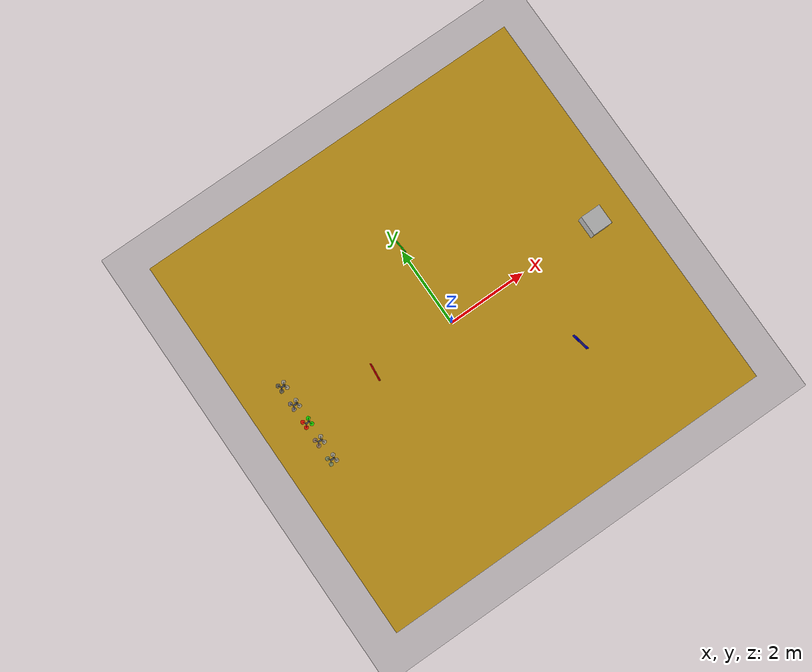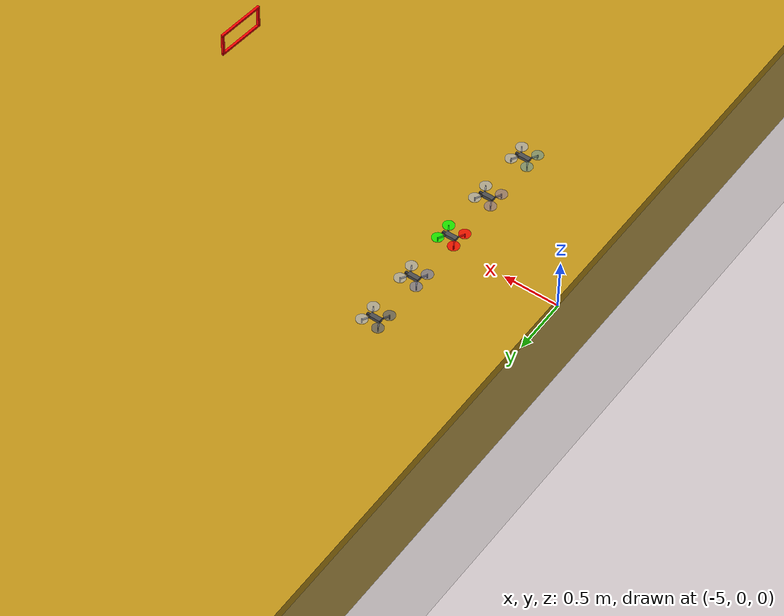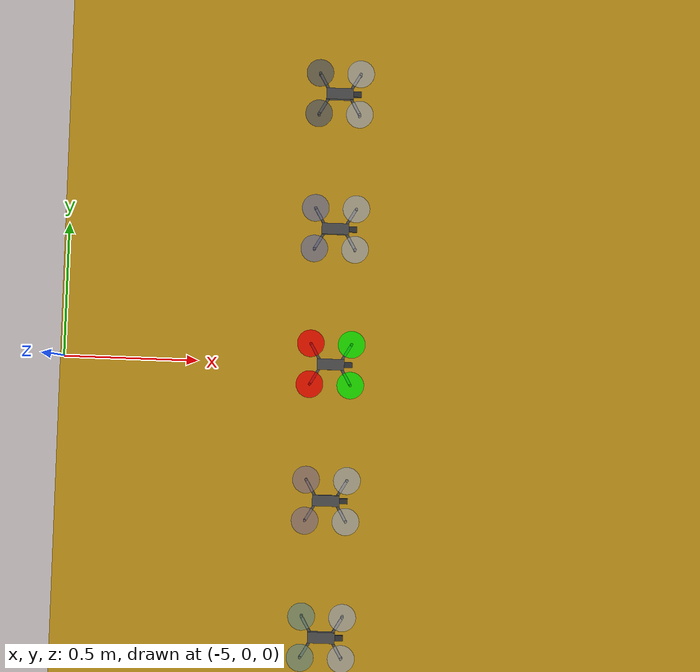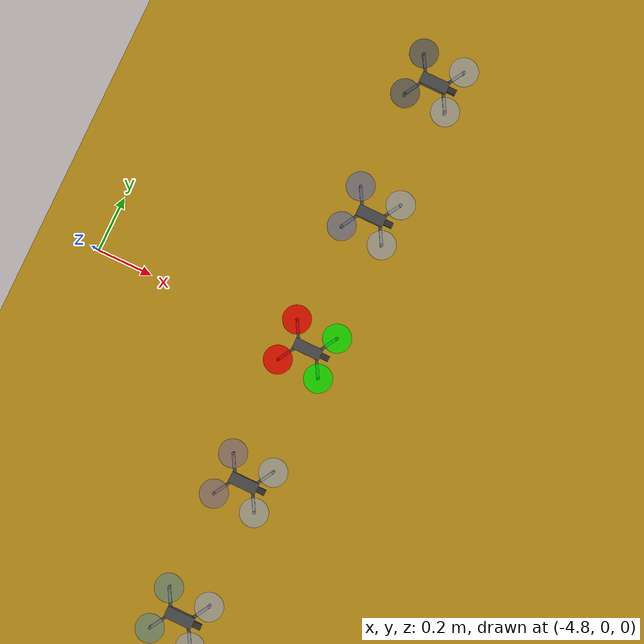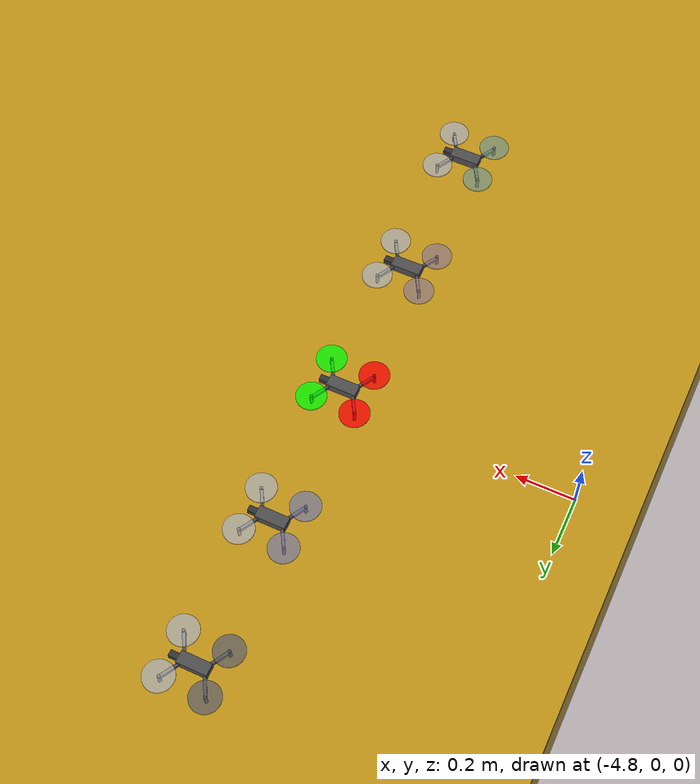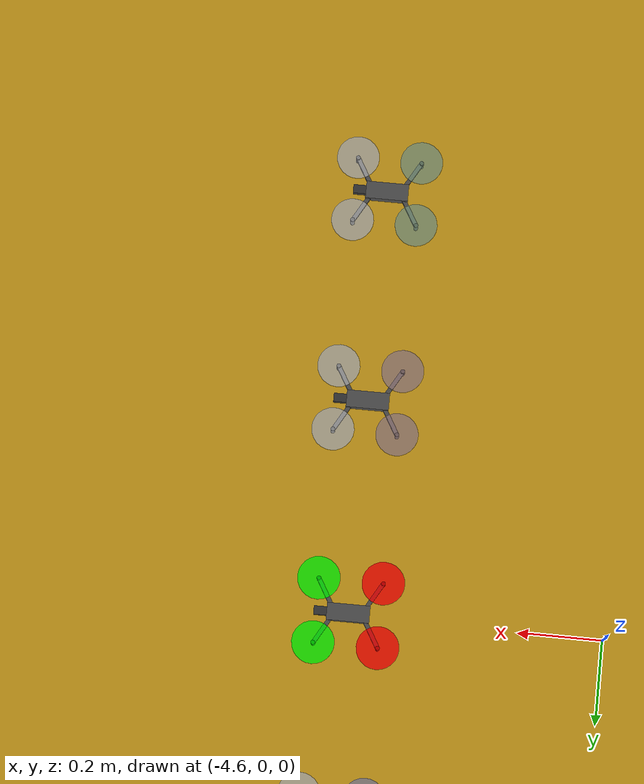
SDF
<sdf version="1.6">
 <world name="I3A world">
  <plugin name="World" filename="libWorld.so"/>
  <include><name>floor</name><uri>../models/DC/floor</uri></include>
  <include><name>tatami</name><uri>../models/DC/tatami</uri><pose>0 0 -0.4 0 0 0</pose></include>
  <include><name>vertiport</name><uri>../models/DC/base_drone</uri><pose>4 0 0.26 0 0 0</pose></include>
  <include><name>frame_red</name><uri>../models/DC/frame_red</uri><pose>-2 0 1.2 0 0 -0.1</pose></include>
  <include><name>frame_green</name><uri>../models/DC/frame_green</uri><pose>0 2 1 0 0 0.1</pose></include>
  <include><name>frame_blue</name><uri>../models/DC/frame_blue</uri><pose>2 -2 1.1 0 0 0.2</pose></include>
  <include><name>abejorro</name><pose>-4 0 0.13 0 0 0</pose><uri>../models/DC/abejorroC</uri></include>
  <include><name>abejorro1</name><uri>../models/DC/abejorro1</uri><pose>-4 1 0.13 0 0 0</pose></include>
  <include><name>abejorro2</name><pose>-4 0.5 0.13 0 0 0</pose><uri>../models/DC/abejorro2</uri></include>
  <include><name>abejorro3</name><pose>-4 -0.5 0.13 0 0 0</pose><uri>../models/DC/abejorro3</uri></include>
  <include><name>abejorro4</name><pose>-4 -1 0.13 0 0 0</pose><uri>../models/DC/abejorro4</uri></include>
  <scene><ambient>0.5 0.5 0.5 1.0</ambient><shadows>true</shadows><origin_visual>false</origin_visual></scene>
  <light type="directional" name="sun">
   <pose>0 0 10 0 0 0</pose>
   <diffuse>1 1 1 1</diffuse>
   <specular>0.2 0.2 0.2 1</specular>
   <attenuation><range>100</range><constant>1</constant></attenuation>
   <direction>0.5 0.1 -0.9</direction>
  </light>
  <physics type="ode">
   <max_step_size>0.001</max_step_size>
   <real_time_update_rate>1000</real_time_update_rate>
  </physics>
 </world>
</sdf>

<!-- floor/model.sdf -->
<sdf version="1.5">

<model name="ground_plane">

<static>true</static>

<link name="link">

  <collision name="collision">

    <geometry>
      <plane>
        <normal>0 0 1</normal>
        <size>200 200</size>
      </plane>
    </geometry>

    <surface>
      <friction>
        <ode>
          <mu>100.0</mu>
          <mu2>50.0</mu2>
          <slip1>0.0</slip1>
          <slip2>0.0</slip2>
        </ode>
      </friction>
    </surface>

  </collision>

  <visual name="visual">

    <cast_shadows>true</cast_shadows>

    <geometry>
      <plane>
        <normal>0 0 1</normal>
        <size>200 200</size>
      </plane>
    </geometry>
    <material>
        <ambient>0.5 0.5 0.5 1</ambient>
        <diffuse>0.5 0.5 0.5 1</diffuse>
    </material>

  </visual>

</link>

</model>
</sdf>

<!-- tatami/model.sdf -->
<sdf version="1.7">

<model name="tatami_model">

  <static>true</static>

  <link name="link">

    <collision name="collision">

      <geometry>
        <box>
          <size>10 10 1</size>
        </box>
      </geometry>

      <surface>
        <friction>
          <ode>
            <mu>100.0</mu>
            <mu2>50.0</mu2>
            <slip1>0.0</slip1>
            <slip2>0.0</slip2>
          </ode>
        </friction>
      </surface>

    </collision>

    <visual name="visual">

      <cast_shadows>true</cast_shadows>

      <geometry>
        <box>
          <size>10 10 1</size>
        </box>
      </geometry>
      <material>
          <ambient>0.76 0.58 0.09 1</ambient>
          <diffuse>0.76 0.58 0.09 1</diffuse>
      </material>

    </visual>

  </link>

</model>
</sdf>

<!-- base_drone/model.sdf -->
<sdf version="1.7">

<model name="base_drone">
	<static>true</static>
	<link name="link">

	<collision name="collision">

		<geometry>
			<box>
			<size>0.50 0.50 0.50</size>
			</box>
		</geometry>

		<surface>
			<friction>
			<ode>
				<mu>100.0</mu>
				<mu2>50.0</mu2>
				<slip1>0.0</slip1>
				<slip2>0.0</slip2>
			</ode>
			</friction>
		</surface>

	</collision>

	<visual name="visual">
		<geometry>
			<box>
			<size>0.50 0.50 0.50</size>
			</box>
		</geometry>
	</visual>

	</link>
</model>

</sdf>

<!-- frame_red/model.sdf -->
<sdf version="1.7">
<model name="frame_red">

<static>true</static>

<link name='framelink'>
    <!-- Marco de 40x20 cms. Borde de 3cms. -->

    <visual name='up'>
        <pose>0 0 0.10 0 0 0</pose>
        <geometry>
          <box>
            <size>0.02 0.42 0.02</size>
          </box>
        </geometry>
        <material>
          <ambient>1 0 0 1</ambient>
          <diffuse>1 0 0 1</diffuse>
        </material>
    </visual>

    <collision name='up'>
        <pose>0 0 0.10 0 0 0</pose>
        <geometry>
          <box>
            <size>0.02 0.42 0.02</size>
          </box>
        </geometry>
        <surface>
          <friction>
            <ode>
              <mu>0.1</mu>
              <mu2>0.2</mu2>
              <slip1>1.0</slip1>
              <slip2>1.0</slip2>
            </ode>
          </friction>
        </surface>
    </collision>

    <visual name='down'>
        <pose>0 0 -0.10 0 0 0</pose>
        <geometry>
          <box>
            <size>0.02 0.42 0.02</size>
          </box>
        </geometry>
        <material>
          <ambient>1 0 0 1</ambient>
          <diffuse>1 0 0 1</diffuse>
        </material>
    </visual>

    <collision name='down'>
        <pose>0 0 -0.10 0 0 0</pose>
        <geometry>
          <box>
            <size>0.02 0.42 0.02</size>
          </box>
        </geometry>
        <surface>
          <friction>
            <ode>
              <mu>0.1</mu>
              <mu2>0.2</mu2>
              <slip1>1.0</slip1>
              <slip2>1.0</slip2>
            </ode>
          </friction>
        </surface>
    </collision>

    <visual name='left'>
        <pose>0 -0.20 0 0 0 0</pose>
        <geometry>
          <box>
            <size>0.02 0.02 0.18</size>
          </box>
        </geometry>
        <material>
          <ambient>1 0 0 1</ambient>
          <diffuse>1 0 0 1</diffuse>
        </material>
    </visual>

    <collision name='left'>
        <pose>0 -0.20 0 0 0 0</pose>
        <geometry>
          <box>
            <size>0.02 0.02 0.18</size>
          </box>
        </geometry>
        <surface>
          <friction>
            <ode>
              <mu>0.1</mu>
              <mu2>0.2</mu2>
              <slip1>1.0</slip1>
              <slip2>1.0</slip2>
            </ode>
          </friction>
        </surface>
    </collision>

    <visual name='right'>
        <pose>0 0.20 0 0 0 0</pose>
        <geometry>
          <box>
            <size>0.02 0.02 0.18</size>
          </box>
        </geometry>
        <material>
          <ambient>1 0 0 1</ambient>
          <diffuse>1 0 0 1</diffuse>
        </material>
    </visual>

    <collision name='right'>
        <pose>0 0.20 0 0 0 0</pose>
        <geometry>
          <box>
            <size>0.02 0.02 0.18</size>
          </box>
        </geometry>
        <surface>
          <friction>
            <ode>
              <mu>0.1</mu>
              <mu2>0.2</mu2>
              <slip1>1.0</slip1>
              <slip2>1.0</slip2>
            </ode>
          </friction>
        </surface>
    </collision>

</link>

</model>

</sdf>

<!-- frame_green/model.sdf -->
<sdf version="1.7">
<model name="frame_green">

<static>true</static>

<link name='framelink'>
    <!-- Marco de 40x20 cms. Borde de 3cms. -->

    <visual name='up'>
        <pose>0 0 0.10 0 0 0</pose>
        <geometry>
          <box>
            <size>0.02 0.42 0.02</size>
          </box>
        </geometry>
        <material>
          <ambient>0 1 0 1</ambient>
          <diffuse>0 1 0 1</diffuse>
        </material>
    </visual>

    <collision name='up'>
        <pose>0 0 0.10 0 0 0</pose>
        <geometry>
          <box>
            <size>0.02 0.42 0.02</size>
          </box>
        </geometry>
        <surface>
          <friction>
            <ode>
              <mu>0.1</mu>
              <mu2>0.2</mu2>
              <slip1>1.0</slip1>
              <slip2>1.0</slip2>
            </ode>
          </friction>
        </surface>
    </collision>

    <visual name='down'>
        <pose>0 0 -0.10 0 0 0</pose>
        <geometry>
          <box>
            <size>0.02 0.42 0.02</size>
          </box>
        </geometry>
        <material>
          <ambient>0 1 0 1</ambient>
          <diffuse>0 1 0 1</diffuse>
        </material>
    </visual>

    <collision name='down'>
        <pose>0 0 -0.10 0 0 0</pose>
        <geometry>
          <box>
            <size>0.02 0.42 0.02</size>
          </box>
        </geometry>
        <surface>
          <friction>
            <ode>
              <mu>0.1</mu>
              <mu2>0.2</mu2>
              <slip1>1.0</slip1>
              <slip2>1.0</slip2>
            </ode>
          </friction>
        </surface>
    </collision>

    <visual name='left'>
        <pose>0 -0.20 0 0 0 0</pose>
        <geometry>
          <box>
            <size>0.02 0.02 0.18</size>
          </box>
        </geometry>
        <material>
          <ambient>0 1 0 1</ambient>
          <diffuse>0 1 0 1</diffuse>
        </material>
    </visual>

    <collision name='left'>
        <pose>0 -0.20 0 0 0 0</pose>
        <geometry>
          <box>
            <size>0.02 0.02 0.18</size>
          </box>
        </geometry>
        <surface>
          <friction>
            <ode>
              <mu>0.1</mu>
              <mu2>0.2</mu2>
              <slip1>1.0</slip1>
              <slip2>1.0</slip2>
            </ode>
          </friction>
        </surface>
    </collision>

    <visual name='right'>
        <pose>0 0.20 0 0 0 0</pose>
        <geometry>
          <box>
            <size>0.02 0.02 0.18</size>
          </box>
        </geometry>
        <material>
          <ambient>0 1 0 1</ambient>
          <diffuse>0 1 0 1</diffuse>
        </material>
    </visual>

    <collision name='right'>
        <pose>0 0.20 0 0 0 0</pose>
        <geometry>
          <box>
            <size>0.02 0.02 0.18</size>
          </box>
        </geometry>
        <surface>
          <friction>
            <ode>
              <mu>0.1</mu>
              <mu2>0.2</mu2>
              <slip1>1.0</slip1>
              <slip2>1.0</slip2>
            </ode>
          </friction>
        </surface>
    </collision>

</link>

</model>

</sdf>

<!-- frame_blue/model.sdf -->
<sdf version="1.6">
<model name="frame_blue">

<static>true</static>

<link name='framelink'>
    <!-- Marco de 40x20 cms. Borde de 3cms. -->

    <visual name='up'>
        <pose>0 0 0.10 0 0 0</pose>
        <geometry>
          <box>
            <size>0.02 0.42 0.02</size>
          </box>
        </geometry>
        <material>
          <ambient>0 0 1 1</ambient>
          <diffuse>0 0 1 1</diffuse>
        </material>
    </visual>

    <collision name='up'>
        <pose>0 0 0.10 0 0 0</pose>
        <geometry>
          <box>
            <size>0.02 0.42 0.02</size>
          </box>
        </geometry>
        <surface>
          <friction>
            <ode>
              <mu>0.1</mu>
              <mu2>0.2</mu2>
              <slip1>1.0</slip1>
              <slip2>1.0</slip2>
            </ode>
          </friction>
        </surface>
    </collision>

    <visual name='down'>
        <pose>0 0 -0.10 0 0 0</pose>
        <geometry>
          <box>
            <size>0.02 0.42 0.02</size>
          </box>
        </geometry>
        <material>
          <ambient>0 0 1 1</ambient>
          <diffuse>0 0 1 1</diffuse>
        </material>
    </visual>

    <collision name='down'>
        <pose>0 0 -0.10 0 0 0</pose>
        <geometry>
          <box>
            <size>0.02 0.42 0.02</size>
          </box>
        </geometry>
        <surface>
          <friction>
            <ode>
              <mu>0.1</mu>
              <mu2>0.2</mu2>
              <slip1>1.0</slip1>
              <slip2>1.0</slip2>
            </ode>
          </friction>
        </surface>
    </collision>

    <visual name='left'>
        <pose>0 -0.20 0 0 0 0</pose>
        <geometry>
          <box>
            <size>0.02 0.02 0.18</size>
          </box>
        </geometry>
        <material>
          <ambient>0 0 1 1</ambient>
          <diffuse>0 0 1 1</diffuse>
        </material>
    </visual>

    <collision name='left'>
        <pose>0 -0.20 0 0 0 0</pose>
        <geometry>
          <box>
            <size>0.02 0.02 0.18</size>
          </box>
        </geometry>
        <surface>
          <friction>
            <ode>
              <mu>0.1</mu>
              <mu2>0.2</mu2>
              <slip1>1.0</slip1>
              <slip2>1.0</slip2>
            </ode>
          </friction>
        </surface>
    </collision>

    <visual name='right'>
        <pose>0 0.20 0 0 0 0</pose>
        <geometry>
          <box>
            <size>0.02 0.02 0.18</size>
          </box>
        </geometry>
        <material>
          <ambient>0 0 1 1</ambient>
          <diffuse>0 0 1 1</diffuse>
        </material>
    </visual>

    <collision name='right'>
        <pose>0 0.20 0 0 0 0</pose>
        <geometry>
          <box>
            <size>0.02 0.02 0.18</size>
          </box>
        </geometry>
        <surface>
          <friction>
            <ode>
              <mu>0.1</mu>
              <mu2>0.2</mu2>
              <slip1>1.0</slip1>
              <slip2>1.0</slip2>
            </ode>
          </friction>
        </surface>
    </collision>

</link>

</model>

</sdf>

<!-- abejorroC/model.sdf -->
<sdf version="1.6">

<model name="abejorroC">

<plugin name="DCdrone" filename="libDCdrone.so">
</plugin>

<static>false</static>

<link name='dronelink'>

<visual name='fuselaje'>
    <pose>0 0 0 0 0 0</pose>
    <geometry>
      <box>
        <size>0.10 0.04 0.03</size>
      </box>
    </geometry>
    <material>
      <ambient>0.3 0.3 0.3 1</ambient>
      <diffuse>0.3 0.3 0.3 1</diffuse>
    </material>
</visual>

<collision name='fuselaje'>
    <pose>0 0 0 0 0 0</pose>
    <geometry>
      <box>
        <size>0.10 0.04 0.03</size>
      </box>
    </geometry>
    <surface>
      <friction>
        <ode>
          <mu>0.1</mu>
          <mu2>0.2</mu2>
          <slip1>1.0</slip1>
          <slip2>1.0</slip2>
        </ode>
      </friction>
    </surface>
</collision>

<visual name='camara'>
    <pose>0.065 0 0 0 0 0</pose>
    <geometry>
      <box>
        <size>0.03 0.02 0.02</size>
      </box>
    </geometry>
    <material>
      <ambient>0.2 0.2 0.2 1</ambient>
      <diffuse>0.2 0.2 0.2 1</diffuse>
    </material>
</visual>

<collision name='camara'>
    <pose>0.065 0 0 0 0 0</pose>
    <geometry>
      <box>
        <size>0.03 0.02 0.02</size>
      </box>
    </geometry>
    <surface>
      <friction>
        <ode>
          <mu>0.1</mu>
          <mu2>0.2</mu2>
          <slip1>1.0</slip1>
          <slip2>1.0</slip2>
        </ode>
      </friction>
    </surface>
</collision>

<sensor name='NavSim/abejorro/onboard_cam' type='camera'>

  <pose>0.08 0 0 0 0 0</pose>
  <camera name='onboard_cam'>
    <horizontal_fov>1.57</horizontal_fov>
    <image>
        <width> 320</width>
        <height>240</height>
    </image>
    <clip>
        <near>0.01</near>
        <far>20</far>
    </clip>
  </camera>
  <update_rate>10</update_rate>
  <always_on>true</always_on>
  <visualize>false</visualize>

  <plugin name="onboard_cam" filename="libgazebo_ros_camera.so">
    <alwaysOn>true</alwaysOn>
    <updateRate>1</updateRate>
    <cameraName>onboard_cam</cameraName>
  </plugin>

</sensor>

<visual name='brazo_NE'>
    <pose>0.0550 -0.0406 0 0 0 -1.0472</pose>
    <geometry>
      <box>
        <size>0.08 .01 .01</size>
      </box>
    </geometry>
    <material>
      <ambient>0.3 0.3 0.3 1</ambient>
      <diffuse>0.3 0.3 0.3 1</diffuse>
    </material>
</visual>

<collision name='brazo_NE'>
    <pose>0.0550 -0.0406 0 0 0 -1.0472</pose>
    <geometry>
      <box>
        <size>0.08 .01 .01</size>
      </box>
    </geometry>
    <surface>
      <friction>
        <ode>
          <mu>0.1</mu>
          <mu2>0.2</mu2>
          <slip1>1.0</slip1>
          <slip2>1.0</slip2>
        </ode>
      </friction>
    </surface>
</collision>

<visual name="motor_NE">
    <pose>0.0750 -0.0750 -0.01 0 0 0</pose>
    <geometry>
        <cylinder>
            <radius>.005</radius>
            <length>.04</length>
        </cylinder>
    </geometry>
    <material>
        <ambient>0 0 0 1</ambient>  <!--color Red Green Blue Alpha [0-1] -->
        <diffuse>0 0 0 1</diffuse>
    </material>
</visual>

<collision name="motor_NE">
    <pose>0.0750 -0.0750 -0.01 0 0 0</pose>
    <geometry>
        <cylinder>
            <radius>.005</radius>
            <length>.04</length>
        </cylinder>
    </geometry>
    <surface>
        <friction>
            <ode>
            <mu>100.0</mu>
            <mu2>50.0</mu2>
            <slip1>0.0</slip1>
            <slip2>0.0</slip2>
            </ode>
        </friction>
    </surface>
</collision>

<visual name="rotor_NE">
    <pose>0.0750 -0.0750 0.01 0 0 0</pose>
    <geometry>
        <cylinder>
            <radius>0.05</radius>
            <length>0.005</length>
        </cylinder>
    </geometry>
    <material>
        <ambient>0 1 0 0.8</ambient>  <!--color Red Green Blue Alpha [0-1] -->
        <diffuse>0 1 0 0.8</diffuse>
    </material>
</visual>

<collision name="rotor_NE">
    <pose>0.0750 -0.0750 0.01 0 0 0</pose>
    <geometry>
        <cylinder>
            <radius>0.05</radius>
            <length>0.005</length>
        </cylinder>
    </geometry>
    <surface>
        <friction>
            <ode>
            <mu>0.1</mu>
            <mu2>0.2</mu2>
            <slip1>1.0</slip1>
            <slip2>1.0</slip2>
            </ode>
        </friction>
    </surface>
</collision>

<visual name='brazo_NW'>
    <pose>0.0550 0.0406 0 0 0 1.0472</pose>
    <geometry>
      <box>
        <size>0.08 0.01 0.01</size>
      </box>
    </geometry>
    <material>
      <ambient>0.3 0.3 0.3 1</ambient>
      <diffuse>0.3 0.3 0.3 1</diffuse>
    </material>
</visual>

<collision name='brazo_NW'>
    <pose>0.0550 0.0406 0 0 0 1.0472</pose>
    <geometry>
      <box>
        <size>0.08 0.01 0.01</size>
      </box>
    </geometry>
    <surface>
      <friction>
        <ode>
          <mu>0.1</mu>
          <mu2>0.2</mu2>
          <slip1>1.0</slip1>
          <slip2>1.0</slip2>
        </ode>
      </friction>
    </surface>
</collision>

<visual name="motor_NW">
    <pose>0.0750 0.0750 -0.01 0 0 0</pose>
    <geometry>
        <cylinder>
            <radius>0.005</radius>
            <length>0.04</length>
        </cylinder>
    </geometry>
    <material>
        <ambient>0 0 0 1</ambient>  <!--color Red Green Blue Alpha [0-1] -->
        <diffuse>0 0 0 1</diffuse>
    </material>
</visual>

<collision name="motor_NW">
    <pose>0.0750 0.0750 -0.01 0 0 0</pose>
    <geometry>
        <cylinder>
            <radius>0.005</radius>
            <length>0.04</length>
        </cylinder>
    </geometry>
    <surface>
        <friction>
            <ode>
            <mu>100.0</mu>
            <mu2>50.0</mu2>
            <slip1>0.0</slip1>
            <slip2>0.0</slip2>
            </ode>
        </friction>
    </surface>
</collision>

<visual name="rotor_NW">
    <pose>0.0750 0.0750 0.01 0 0 0</pose>
    <geometry>
        <cylinder>
            <radius>0.05</radius>
            <length>0.005</length>
        </cylinder>
    </geometry>
    <material>
        <ambient>0 1 0 0.8</ambient>  <!--color Red Green Blue Alpha [0-1] -->
        <diffuse>0 1 0 0.8</diffuse>
    </material>
</visual>

<collision name="rotor_NW">
    <pose>0.0750 0.0750 0.01 0 0 0</pose>
    <geometry>
        <cylinder>
            <radius>0.05</radius>
            <length>0.005</length>
        </cylinder>
    </geometry>
    <surface>
        <friction>
            <ode>
            <mu>0.1</mu>
            <mu2>0.2</mu2>
            <slip1>1.0</slip1>
            <slip2>1.0</slip2>
            </ode>
        </friction>
    </surface>
</collision>

<visual name='brazo_SE'>
    <pose>-0.0550 -0.0406 0 0 0 1.0472</pose>
    <geometry>
      <box>
        <size>0.08 0.01 0.01</size>
      </box>
    </geometry>
    <material>
      <ambient>0.3 0.3 0.3 1</ambient>
      <diffuse>0.3 0.3 0.3 1</diffuse>
    </material>
</visual>

<collision name='brazo_SE'>
    <pose>-0.0550 -0.0406 0 0 0 1.0472</pose>
    <geometry>
      <box>
        <size>0.08 0.01 0.01</size>
      </box>
    </geometry>
    <surface>
      <friction>
        <ode>
          <mu>0.1</mu>
          <mu2>0.2</mu2>
          <slip1>1.0</slip1>
          <slip2>1.0</slip2>
        </ode>
      </friction>
    </surface>
</collision>

<visual name="motor_SE">
    <pose>-0.0750 -0.0750 -0.01 0 0 0</pose>
    <geometry>
        <cylinder>
            <radius>0.005</radius>
            <length>0.04</length>
        </cylinder>
    </geometry>
    <material>
        <ambient>0 0 0 1</ambient>  <!--color Red Green Blue Alpha [0-1] -->
        <diffuse>0 0 0 1</diffuse>
    </material>
</visual>

<collision name="motor_SE">
    <pose>-0.0750 -0.0750 -0.01 0 0 0</pose>
    <geometry>
        <cylinder>
            <radius>0.005</radius>
            <length>0.04</length>
        </cylinder>
    </geometry>
    <surface>
        <friction>
            <ode>
            <mu>100.0</mu>
            <mu2>50.0</mu2>
            <slip1>0.0</slip1>
            <slip2>0.0</slip2>
            </ode>
        </friction>
    </surface>
</collision>

<visual name="rotor_SE">
    <pose>-0.0750 -0.0750 0.01 0 0 0</pose>
    <geometry>
        <cylinder>
            <radius>0.05</radius>
            <length>.005</length>
        </cylinder>
    </geometry>
    <material>
        <ambient>1 0 0 0.8</ambient>  <!--color Red Green Blue Alpha [0-1] -->
        <diffuse>1 0 0 0.8</diffuse>
    </material>
</visual>

<collision name="rotor_SE">
    <pose>-0.0750 -0.0750 0.01 0 0 0</pose>
    <geometry>
        <cylinder>
            <radius>0.05</radius>
            <length>0.005</length>
        </cylinder>
    </geometry>
    <surface>
        <friction>
            <ode>
            <mu>0.1</mu>
            <mu2>0.2</mu2>
            <slip1>1.0</slip1>
            <slip2>1.0</slip2>
            </ode>
        </friction>
    </surface>
</collision>

<visual name='brazo_SW'>
    <pose>-0.0550 0.0406 0 0 0 -1.0472</pose>
    <geometry>
      <box>
        <size>0.08 0.01 0.01</size>
      </box>
    </geometry>
    <material>
      <ambient>0.3 0.3 0.3 1</ambient>
      <diffuse>0.3 0.3 0.3 1</diffuse>
    </material>
</visual>

<collision name='brazo_SW'>
    <pose>-0.0550 0.0406 0 0 0 -1.0472</pose>
    <geometry>
      <box>
        <size>0.08 0.01 0.01</size>
      </box>
    </geometry>
    <surface>
      <friction>
        <ode>
          <mu>0.1</mu>
          <mu2>0.2</mu2>
          <slip1>1.0</slip1>
          <slip2>1.0</slip2>
        </ode>
      </friction>
    </surface>
</collision>

<visual name="motor_SW">
    <pose>-0.0750 0.0750 -0.01 0 0 0</pose>
    <geometry>
        <cylinder>
            <radius>0.005</radius>
            <length>0.04</length>
        </cylinder>
    </geometry>
    <material>
        <ambient>0 0 0 1</ambient>  <!--color Red Green Blue Alpha [0-1] -->
        <diffuse>0 0 0 1</diffuse>
    </material>
</visual>

<collision name="motor_SW">
    <pose>-0.0750 0.0750 -0.01 0 0 0</pose>
    <geometry>
        <cylinder>
            <radius>0.005</radius>
            <length>0.04</length>
        </cylinder>
    </geometry>
    <surface>
        <friction>
            <ode>
            <mu>100.0</mu>
            <mu2>50.0</mu2>
            <slip1>0.0</slip1>
            <slip2>0.0</slip2>
            </ode>
        </friction>
    </surface>
</collision>

<visual name="rotor_SW">
    <pose>-0.0750 0.0750 0.01 0 0 0</pose>
    <geometry>
        <cylinder>
            <radius>0.05</radius>
            <length>0.005</length>
        </cylinder>
    </geometry>
    <material>
        <ambient>1 0 0 0.8</ambient>  <!--color Red Green Blue Alpha [0-1] -->
        <diffuse>1 0 0 0.8</diffuse>
    </material>
</visual>

<collision name="rotor_SW">
    <pose>-0.0750 0.0750 0.01 0 0 0</pose>
    <geometry>
        <cylinder>
            <radius>0.05</radius>
            <length>0.005</length>
        </cylinder>
    </geometry>
    <surface>
        <friction>
            <ode>
            <mu>0.1</mu>
            <mu2>0.2</mu2>
            <slip1>1.0</slip1>
            <slip2>1.0</slip2>
            </ode>
        </friction>
    </surface>
</collision>

<inertial>
  <mass>0.300</mass>

  <inertia>                <!-- http://en.wikipedia.org/wiki/List_of_moments_of_inertia -->
    <ixx>0.001022500</ixx> <!-- for a box: ixx = 1/12 * mass * (y*y + z*z) -->
    <ixy>0.0</ixy>         <!-- for a box: ixy = 0 -->
    <ixz>0.0</ixz>         <!-- for a box: ixz = 0 -->
    <iyy>0.001022500</iyy> <!-- for a box: iyy = 1/12 * mass * (x*x + z*z) -->
    <iyz>0.0</iyz>         <!-- for a box: iyz = 0 -->
    <izz>0.002000000</izz> <!-- for a box: izz = 1/12 * mass * (x*x + y*y) -->
  </inertia>
</inertial>

</link>

</model>

</sdf>

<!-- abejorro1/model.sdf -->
<sdf version="1.7">

<model name="abejorro1">

<plugin name="DCdrone" filename="libDCdrone.so">
</plugin>

<static>false</static>

<link name='dronelink'>

<visual name='fuselaje'>
    <pose>0 0 0 0 0 0</pose>
    <geometry>
      <box>
        <size>0.10 0.04 0.03</size>
      </box>
    </geometry>
    <material>
      <ambient>0.3 0.3 0.3 1</ambient>
      <diffuse>0.3 0.3 0.3 1</diffuse>
    </material>
</visual>

<collision name='fuselaje'>
    <pose>0 0 0 0 0 0</pose>
    <geometry>
      <box>
        <size>0.10 0.04 0.03</size>
      </box>
    </geometry>
    <surface>
      <friction>
        <ode>
          <mu>0.1</mu>
          <mu2>0.2</mu2>
          <slip1>1.0</slip1>
          <slip2>1.0</slip2>
        </ode>
      </friction>
    </surface>
</collision>

<visual name='camara'>
    <pose>0.065 0 0 0 0 0</pose>
    <geometry>
      <box>
        <size>0.03 0.02 0.02</size>
      </box>
    </geometry>
    <material>
      <ambient>0.2 0.2 0.2 1</ambient>
      <diffuse>0.2 0.2 0.2 1</diffuse>
    </material>
</visual>

<collision name='camara'>
    <pose>0.065 0 0 0 0 0</pose>
    <geometry>
      <box>
        <size>0.03 0.02 0.02</size>
      </box>
    </geometry>
    <surface>
      <friction>
        <ode>
          <mu>0.1</mu>
          <mu2>0.2</mu2>
          <slip1>1.0</slip1>
          <slip2>1.0</slip2>
        </ode>
      </friction>
    </surface>
</collision>

<sensor name='NavSim/abejorro1/follow_cam' type='camera'>

  <pose>-0.20 0 0.08 0 0 0</pose>
  <camera name='follow_cam1'>
    <horizontal_fov>1.57</horizontal_fov>
    <image>
        <width> 480</width>
        <height>320</height>
    </image>
    <clip>
        <near>0.05</near>
        <far>200</far>
    </clip>
  </camera>
  <update_rate>10</update_rate>
  <always_on>true</always_on>
  <visualize>false</visualize>

  <plugin name="follow_cam1" filename="libgazebo_ros_camera.so">
    <alwaysOn>true</alwaysOn>
    <updateRate>1</updateRate>
    <cameraName>follow_cam1</cameraName>
  </plugin>

</sensor>

<visual name='brazo_NE'>
    <pose>0.0550 -0.0406 0 0 0 -1.0472</pose>
    <geometry>
      <box>
        <size>0.08 .01 .01</size>
      </box>
    </geometry>
    <material>
      <ambient>0.3 0.3 0.3 1</ambient>
      <diffuse>0.3 0.3 0.3 1</diffuse>
    </material>
</visual>

<collision name='brazo_NE'>
    <pose>0.0550 -0.0406 0 0 0 -1.0472</pose>
    <geometry>
      <box>
        <size>0.08 .01 .01</size>
      </box>
    </geometry>
    <surface>
      <friction>
        <ode>
          <mu>0.1</mu>
          <mu2>0.2</mu2>
          <slip1>1.0</slip1>
          <slip2>1.0</slip2>
        </ode>
      </friction>
    </surface>
</collision>

<visual name="motor_NE">
    <pose>0.0750 -0.0750 -0.01 0 0 0</pose>
    <geometry>
        <cylinder>
            <radius>.005</radius>
            <length>.04</length>
        </cylinder>
    </geometry>
    <material>
        <ambient>0 0 0 1</ambient>  <!--color Red Green Blue Alpha [0-1] -->
        <diffuse>0 0 0 1</diffuse>
    </material>
</visual>

<collision name="motor_NE">
    <pose>0.0750 -0.0750 -0.01 0 0 0</pose>
    <geometry>
        <cylinder>
            <radius>.005</radius>
            <length>.04</length>
        </cylinder>
    </geometry>
    <surface>
        <friction>
            <ode>
            <mu>100.0</mu>
            <mu2>50.0</mu2>
            <slip1>0.0</slip1>
            <slip2>0.0</slip2>
            </ode>
        </friction>
    </surface>
</collision>

<visual name="rotor_NE">
    <pose>0.0750 -0.0750 0.01 0 0 0</pose>
    <geometry>
        <cylinder>
            <radius>0.05</radius>
            <length>0.005</length>
        </cylinder>
    </geometry>
    <material>
      <ambient>0.7 0.7 0.7 0.8</ambient>  <!--color Red Green Blue Alpha [0-1] -->
      <diffuse>0.7 0.7 0.7 0.8</diffuse>
  </material>
</visual>

<collision name="rotor_NE">
    <pose>0.0750 -0.0750 0.01 0 0 0</pose>
    <geometry>
        <cylinder>
            <radius>0.05</radius>
            <length>0.005</length>
        </cylinder>
    </geometry>
    <surface>
        <friction>
            <ode>
            <mu>0.1</mu>
            <mu2>0.2</mu2>
            <slip1>1.0</slip1>
            <slip2>1.0</slip2>
            </ode>
        </friction>
    </surface>
</collision>

<visual name='brazo_NW'>
    <pose>0.0550 0.0406 0 0 0 1.0472</pose>
    <geometry>
      <box>
        <size>0.08 0.01 0.01</size>
      </box>
    </geometry>
    <material>
      <ambient>0.3 0.3 0.3 1</ambient>
      <diffuse>0.3 0.3 0.3 1</diffuse>
    </material>
</visual>

<collision name='brazo_NW'>
    <pose>0.0550 0.0406 0 0 0 1.0472</pose>
    <geometry>
      <box>
        <size>0.08 0.01 0.01</size>
      </box>
    </geometry>
    <surface>
      <friction>
        <ode>
          <mu>0.1</mu>
          <mu2>0.2</mu2>
          <slip1>1.0</slip1>
          <slip2>1.0</slip2>
        </ode>
      </friction>
    </surface>
</collision>

<visual name="motor_NW">
    <pose>0.0750 0.0750 -0.01 0 0 0</pose>
    <geometry>
        <cylinder>
            <radius>0.005</radius>
            <length>0.04</length>
        </cylinder>
    </geometry>
    <material>
        <ambient>0 0 0 1</ambient>  <!--color Red Green Blue Alpha [0-1] -->
        <diffuse>0 0 0 1</diffuse>
    </material>
</visual>

<collision name="motor_NW">
    <pose>0.0750 0.0750 -0.01 0 0 0</pose>
    <geometry>
        <cylinder>
            <radius>0.005</radius>
            <length>0.04</length>
        </cylinder>
    </geometry>
    <surface>
        <friction>
            <ode>
            <mu>100.0</mu>
            <mu2>50.0</mu2>
            <slip1>0.0</slip1>
            <slip2>0.0</slip2>
            </ode>
        </friction>
    </surface>
</collision>

<visual name="rotor_NW">
    <pose>0.0750 0.0750 0.01 0 0 0</pose>
    <geometry>
        <cylinder>
            <radius>0.05</radius>
            <length>0.005</length>
        </cylinder>
    </geometry>
    <material>
      <ambient>0.7 0.7 0.7 0.8</ambient>  <!--color Red Green Blue Alpha [0-1] -->
      <diffuse>0.7 0.7 0.7 0.8</diffuse>
  </material>
</visual>

<collision name="rotor_NW">
    <pose>0.0750 0.0750 0.01 0 0 0</pose>
    <geometry>
        <cylinder>
            <radius>0.05</radius>
            <length>0.005</length>
        </cylinder>
    </geometry>
    <surface>
        <friction>
            <ode>
            <mu>0.1</mu>
            <mu2>0.2</mu2>
            <slip1>1.0</slip1>
            <slip2>1.0</slip2>
            </ode>
        </friction>
    </surface>
</collision>

<visual name='brazo_SE'>
    <pose>-0.0550 -0.0406 0 0 0 1.0472</pose>
    <geometry>
      <box>
        <size>0.08 0.01 0.01</size>
      </box>
    </geometry>
    <material>
      <ambient>0.3 0.3 0.3 1</ambient>
      <diffuse>0.3 0.3 0.3 1</diffuse>
    </material>
</visual>

<collision name='brazo_SE'>
    <pose>-0.0550 -0.0406 0 0 0 1.0472</pose>
    <geometry>
      <box>
        <size>0.08 0.01 0.01</size>
      </box>
    </geometry>
    <surface>
      <friction>
        <ode>
          <mu>0.1</mu>
          <mu2>0.2</mu2>
          <slip1>1.0</slip1>
          <slip2>1.0</slip2>
        </ode>
      </friction>
    </surface>
</collision>

<visual name="motor_SE">
    <pose>-0.0750 -0.0750 -0.01 0 0 0</pose>
    <geometry>
        <cylinder>
            <radius>0.005</radius>
            <length>0.04</length>
        </cylinder>
    </geometry>
    <material>
        <ambient>0 0 0 1</ambient>  <!--color Red Green Blue Alpha [0-1] -->
        <diffuse>0 0 0 1</diffuse>
    </material>
</visual>

<collision name="motor_SE">
    <pose>-0.0750 -0.0750 -0.01 0 0 0</pose>
    <geometry>
        <cylinder>
            <radius>0.005</radius>
            <length>0.04</length>
        </cylinder>
    </geometry>
    <surface>
        <friction>
            <ode>
            <mu>100.0</mu>
            <mu2>50.0</mu2>
            <slip1>0.0</slip1>
            <slip2>0.0</slip2>
            </ode>
        </friction>
    </surface>
</collision>

<visual name="rotor_SE">
    <pose>-0.0750 -0.0750 0.01 0 0 0</pose>
    <geometry>
        <cylinder>
            <radius>0.05</radius>
            <length>.005</length>
        </cylinder>
    </geometry>
    <material>
        <ambient>0.4 0.4 0.4 0.8</ambient>  <!--color Red Green Blue Alpha [0-1] -->
        <diffuse>0.4 0.4 0.4 0.8</diffuse>
    </material>
</visual>

<collision name="rotor_SE">
    <pose>-0.0750 -0.0750 0.01 0 0 0</pose>
    <geometry>
        <cylinder>
            <radius>0.05</radius>
            <length>0.005</length>
        </cylinder>
    </geometry>
    <surface>
        <friction>
            <ode>
            <mu>0.1</mu>
            <mu2>0.2</mu2>
            <slip1>1.0</slip1>
            <slip2>1.0</slip2>
            </ode>
        </friction>
    </surface>
</collision>

<visual name='brazo_SW'>
    <pose>-0.0550 0.0406 0 0 0 -1.0472</pose>
    <geometry>
      <box>
        <size>0.08 0.01 0.01</size>
      </box>
    </geometry>
    <material>
      <ambient>0.3 0.3 0.3 1</ambient>
      <diffuse>0.3 0.3 0.3 1</diffuse>
    </material>
</visual>

<collision name='brazo_SW'>
    <pose>-0.0550 0.0406 0 0 0 -1.0472</pose>
    <geometry>
      <box>
        <size>0.08 0.01 0.01</size>
      </box>
    </geometry>
    <surface>
      <friction>
        <ode>
          <mu>0.1</mu>
          <mu2>0.2</mu2>
          <slip1>1.0</slip1>
          <slip2>1.0</slip2>
        </ode>
      </friction>
    </surface>
</collision>

<visual name="motor_SW">
    <pose>-0.0750 0.0750 -0.01 0 0 0</pose>
    <geometry>
        <cylinder>
            <radius>0.005</radius>
            <length>0.04</length>
        </cylinder>
    </geometry>
    <material>
        <ambient>0 0 0 1</ambient>  <!--color Red Green Blue Alpha [0-1] -->
        <diffuse>0 0 0 1</diffuse>
    </material>
</visual>

<collision name="motor_SW">
    <pose>-0.0750 0.0750 -0.01 0 0 0</pose>
    <geometry>
        <cylinder>
            <radius>0.005</radius>
            <length>0.04</length>
        </cylinder>
    </geometry>
    <surface>
        <friction>
            <ode>
            <mu>100.0</mu>
            <mu2>50.0</mu2>
            <slip1>0.0</slip1>
            <slip2>0.0</slip2>
            </ode>
        </friction>
    </surface>
</collision>

<visual name="rotor_SW">
    <pose>-0.0750 0.0750 0.01 0 0 0</pose>
    <geometry>
        <cylinder>
            <radius>0.05</radius>
            <length>0.005</length>
        </cylinder>
    </geometry>
    <material>
      <ambient>0.4 0.4 0.4 0.8</ambient>  <!--color Red Green Blue Alpha [0-1] -->
      <diffuse>0.4 0.4 0.4 0.8</diffuse>
  </material>
</visual>

<collision name="rotor_SW">
    <pose>-0.0750 0.0750 0.01 0 0 0</pose>
    <geometry>
        <cylinder>
            <radius>0.05</radius>
            <length>0.005</length>
        </cylinder>
    </geometry>
    <surface>
        <friction>
            <ode>
            <mu>0.1</mu>
            <mu2>0.2</mu2>
            <slip1>1.0</slip1>
            <slip2>1.0</slip2>
            </ode>
        </friction>
    </surface>
</collision>

<inertial>
  <mass>0.300</mass>

  <inertia>                <!-- http://en.wikipedia.org/wiki/List_of_moments_of_inertia -->
    <ixx>0.001022500</ixx> <!-- for a box: ixx = 1/12 * mass * (y*y + z*z) -->
    <ixy>0.0</ixy>         <!-- for a box: ixy = 0 -->
    <ixz>0.0</ixz>         <!-- for a box: ixz = 0 -->
    <iyy>0.001022500</iyy> <!-- for a box: iyy = 1/12 * mass * (x*x + z*z) -->
    <iyz>0.0</iyz>         <!-- for a box: iyz = 0 -->
    <izz>0.002000000</izz> <!-- for a box: izz = 1/12 * mass * (x*x + y*y) -->
  </inertia>
</inertial>

</link>

</model>

</sdf>

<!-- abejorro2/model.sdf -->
<sdf version="1.7">

<model name="abejorro2">

<plugin name="DCdrone" filename="libDCdrone.so">
</plugin>

<static>false</static>

<link name='dronelink'>

<visual name='fuselaje'>
    <pose>0 0 0 0 0 0</pose>
    <geometry>
      <box>
        <size>0.10 0.04 0.03</size>
      </box>
    </geometry>
    <material>
      <ambient>0.3 0.3 0.3 1</ambient>
      <diffuse>0.3 0.3 0.3 1</diffuse>
    </material>
</visual>

<collision name='fuselaje'>
    <pose>0 0 0 0 0 0</pose>
    <geometry>
      <box>
        <size>0.10 0.04 0.03</size>
      </box>
    </geometry>
    <surface>
      <friction>
        <ode>
          <mu>0.1</mu>
          <mu2>0.2</mu2>
          <slip1>1.0</slip1>
          <slip2>1.0</slip2>
        </ode>
      </friction>
    </surface>
</collision>

<visual name='camara'>
    <pose>0.065 0 0 0 0 0</pose>
    <geometry>
      <box>
        <size>0.03 0.02 0.02</size>
      </box>
    </geometry>
    <material>
      <ambient>0.2 0.2 0.2 1</ambient>
      <diffuse>0.2 0.2 0.2 1</diffuse>
    </material>
</visual>

<collision name='camara'>
    <pose>0.065 0 0 0 0 0</pose>
    <geometry>
      <box>
        <size>0.03 0.02 0.02</size>
      </box>
    </geometry>
    <surface>
      <friction>
        <ode>
          <mu>0.1</mu>
          <mu2>0.2</mu2>
          <slip1>1.0</slip1>
          <slip2>1.0</slip2>
        </ode>
      </friction>
    </surface>
</collision>

<sensor name='NavSim/abejorro2/follow_cam' type='camera'>

  <pose>-0.20 0 0.08 0 0 0</pose>
  <camera name='follow_cam2'>
    <horizontal_fov>1.57</horizontal_fov>
    <image>
        <width> 480</width>
        <height>320</height>
    </image>
    <clip>
        <near>0.05</near>
        <far>200</far>
    </clip>
  </camera>
  <update_rate>10</update_rate>
  <always_on>true</always_on>
  <visualize>false</visualize>

  <plugin name="follow_cam2" filename="libgazebo_ros_camera.so">
    <alwaysOn>true</alwaysOn>
    <updateRate>1</updateRate>
    <cameraName>follow_cam2</cameraName>
  </plugin>

</sensor>

<visual name='brazo_NE'>
    <pose>0.0550 -0.0406 0 0 0 -1.0472</pose>
    <geometry>
      <box>
        <size>0.08 .01 .01</size>
      </box>
    </geometry>
    <material>
      <ambient>0.3 0.3 0.3 1</ambient>
      <diffuse>0.3 0.3 0.3 1</diffuse>
    </material>
</visual>

<collision name='brazo_NE'>
    <pose>0.0550 -0.0406 0 0 0 -1.0472</pose>
    <geometry>
      <box>
        <size>0.08 .01 .01</size>
      </box>
    </geometry>
    <surface>
      <friction>
        <ode>
          <mu>0.1</mu>
          <mu2>0.2</mu2>
          <slip1>1.0</slip1>
          <slip2>1.0</slip2>
        </ode>
      </friction>
    </surface>
</collision>

<visual name="motor_NE">
    <pose>0.0750 -0.0750 -0.01 0 0 0</pose>
    <geometry>
        <cylinder>
            <radius>.005</radius>
            <length>.04</length>
        </cylinder>
    </geometry>
    <material>
        <ambient>0 0 0 1</ambient>  <!--color Red Green Blue Alpha [0-1] -->
        <diffuse>0 0 0 1</diffuse>
    </material>
</visual>

<collision name="motor_NE">
    <pose>0.0750 -0.0750 -0.01 0 0 0</pose>
    <geometry>
        <cylinder>
            <radius>.005</radius>
            <length>.04</length>
        </cylinder>
    </geometry>
    <surface>
        <friction>
            <ode>
            <mu>100.0</mu>
            <mu2>50.0</mu2>
            <slip1>0.0</slip1>
            <slip2>0.0</slip2>
            </ode>
        </friction>
    </surface>
</collision>

<visual name="rotor_NE">
    <pose>0.0750 -0.0750 0.01 0 0 0</pose>
    <geometry>
        <cylinder>
            <radius>0.05</radius>
            <length>0.005</length>
        </cylinder>
    </geometry>
    <material>
      <ambient>0.7 0.7 0.7 0.8</ambient>  <!--color Red Green Blue Alpha [0-1] -->
      <diffuse>0.7 0.7 0.7 0.8</diffuse>
  </material>
</visual>

<collision name="rotor_NE">
    <pose>0.0750 -0.0750 0.01 0 0 0</pose>
    <geometry>
        <cylinder>
            <radius>0.05</radius>
            <length>0.005</length>
        </cylinder>
    </geometry>
    <surface>
        <friction>
            <ode>
            <mu>0.1</mu>
            <mu2>0.2</mu2>
            <slip1>1.0</slip1>
            <slip2>1.0</slip2>
            </ode>
        </friction>
    </surface>
</collision>

<visual name='brazo_NW'>
    <pose>0.0550 0.0406 0 0 0 1.0472</pose>
    <geometry>
      <box>
        <size>0.08 0.01 0.01</size>
      </box>
    </geometry>
    <material>
      <ambient>0.3 0.3 0.3 1</ambient>
      <diffuse>0.3 0.3 0.3 1</diffuse>
    </material>
</visual>

<collision name='brazo_NW'>
    <pose>0.0550 0.0406 0 0 0 1.0472</pose>
    <geometry>
      <box>
        <size>0.08 0.01 0.01</size>
      </box>
    </geometry>
    <surface>
      <friction>
        <ode>
          <mu>0.1</mu>
          <mu2>0.2</mu2>
          <slip1>1.0</slip1>
          <slip2>1.0</slip2>
        </ode>
      </friction>
    </surface>
</collision>

<visual name="motor_NW">
    <pose>0.0750 0.0750 -0.01 0 0 0</pose>
    <geometry>
        <cylinder>
            <radius>0.005</radius>
            <length>0.04</length>
        </cylinder>
    </geometry>
    <material>
        <ambient>0 0 0 1</ambient>  <!--color Red Green Blue Alpha [0-1] -->
        <diffuse>0 0 0 1</diffuse>
    </material>
</visual>

<collision name="motor_NW">
    <pose>0.0750 0.0750 -0.01 0 0 0</pose>
    <geometry>
        <cylinder>
            <radius>0.005</radius>
            <length>0.04</length>
        </cylinder>
    </geometry>
    <surface>
        <friction>
            <ode>
            <mu>100.0</mu>
            <mu2>50.0</mu2>
            <slip1>0.0</slip1>
            <slip2>0.0</slip2>
            </ode>
        </friction>
    </surface>
</collision>

<visual name="rotor_NW">
    <pose>0.0750 0.0750 0.01 0 0 0</pose>
    <geometry>
        <cylinder>
            <radius>0.05</radius>
            <length>0.005</length>
        </cylinder>
    </geometry>
    <material>
      <ambient>0.7 0.7 0.7 0.8</ambient>  <!--color Red Green Blue Alpha [0-1] -->
      <diffuse>0.7 0.7 0.7 0.8</diffuse>
  </material>
</visual>

<collision name="rotor_NW">
    <pose>0.0750 0.0750 0.01 0 0 0</pose>
    <geometry>
        <cylinder>
            <radius>0.05</radius>
            <length>0.005</length>
        </cylinder>
    </geometry>
    <surface>
        <friction>
            <ode>
            <mu>0.1</mu>
            <mu2>0.2</mu2>
            <slip1>1.0</slip1>
            <slip2>1.0</slip2>
            </ode>
        </friction>
    </surface>
</collision>

<visual name='brazo_SE'>
    <pose>-0.0550 -0.0406 0 0 0 1.0472</pose>
    <geometry>
      <box>
        <size>0.08 0.01 0.01</size>
      </box>
    </geometry>
    <material>
      <ambient>0.3 0.3 0.3 1</ambient>
      <diffuse>0.3 0.3 0.3 1</diffuse>
    </material>
</visual>

<collision name='brazo_SE'>
    <pose>-0.0550 -0.0406 0 0 0 1.0472</pose>
    <geometry>
      <box>
        <size>0.08 0.01 0.01</size>
      </box>
    </geometry>
    <surface>
      <friction>
        <ode>
          <mu>0.1</mu>
          <mu2>0.2</mu2>
          <slip1>1.0</slip1>
          <slip2>1.0</slip2>
        </ode>
      </friction>
    </surface>
</collision>

<visual name="motor_SE">
    <pose>-0.0750 -0.0750 -0.01 0 0 0</pose>
    <geometry>
        <cylinder>
            <radius>0.005</radius>
            <length>0.04</length>
        </cylinder>
    </geometry>
    <material>
        <ambient>0 0 0 1</ambient>  <!--color Red Green Blue Alpha [0-1] -->
        <diffuse>0 0 0 1</diffuse>
    </material>
</visual>

<collision name="motor_SE">
    <pose>-0.0750 -0.0750 -0.01 0 0 0</pose>
    <geometry>
        <cylinder>
            <radius>0.005</radius>
            <length>0.04</length>
        </cylinder>
    </geometry>
    <surface>
        <friction>
            <ode>
            <mu>100.0</mu>
            <mu2>50.0</mu2>
            <slip1>0.0</slip1>
            <slip2>0.0</slip2>
            </ode>
        </friction>
    </surface>
</collision>

<visual name="rotor_SE">
    <pose>-0.0750 -0.0750 0.01 0 0 0</pose>
    <geometry>
        <cylinder>
            <radius>0.05</radius>
            <length>.005</length>
        </cylinder>
    </geometry>
    <material>
      <ambient>0.5 0.5 0.6 0.8</ambient>  <!--color Red Green Blue Alpha [0-1] -->
      <diffuse>0.5 0.5 0.6 0.8</diffuse>
  </material>
</visual>

<collision name="rotor_SE">
    <pose>-0.0750 -0.0750 0.01 0 0 0</pose>
    <geometry>
        <cylinder>
            <radius>0.05</radius>
            <length>0.005</length>
        </cylinder>
    </geometry>
    <surface>
        <friction>
            <ode>
            <mu>0.1</mu>
            <mu2>0.2</mu2>
            <slip1>1.0</slip1>
            <slip2>1.0</slip2>
            </ode>
        </friction>
    </surface>
</collision>

<visual name='brazo_SW'>
    <pose>-0.0550 0.0406 0 0 0 -1.0472</pose>
    <geometry>
      <box>
        <size>0.08 0.01 0.01</size>
      </box>
    </geometry>
    <material>
      <ambient>0.3 0.3 0.3 1</ambient>
      <diffuse>0.3 0.3 0.3 1</diffuse>
    </material>
</visual>

<collision name='brazo_SW'>
    <pose>-0.0550 0.0406 0 0 0 -1.0472</pose>
    <geometry>
      <box>
        <size>0.08 0.01 0.01</size>
      </box>
    </geometry>
    <surface>
      <friction>
        <ode>
          <mu>0.1</mu>
          <mu2>0.2</mu2>
          <slip1>1.0</slip1>
          <slip2>1.0</slip2>
        </ode>
      </friction>
    </surface>
</collision>

<visual name="motor_SW">
    <pose>-0.0750 0.0750 -0.01 0 0 0</pose>
    <geometry>
        <cylinder>
            <radius>0.005</radius>
            <length>0.04</length>
        </cylinder>
    </geometry>
    <material>
        <ambient>0 0 0 1</ambient>  <!--color Red Green Blue Alpha [0-1] -->
        <diffuse>0 0 0 1</diffuse>
    </material>
</visual>

<collision name="motor_SW">
    <pose>-0.0750 0.0750 -0.01 0 0 0</pose>
    <geometry>
        <cylinder>
            <radius>0.005</radius>
            <length>0.04</length>
        </cylinder>
    </geometry>
    <surface>
        <friction>
            <ode>
            <mu>100.0</mu>
            <mu2>50.0</mu2>
            <slip1>0.0</slip1>
            <slip2>0.0</slip2>
            </ode>
        </friction>
    </surface>
</collision>

<visual name="rotor_SW">
    <pose>-0.0750 0.0750 0.01 0 0 0</pose>
    <geometry>
        <cylinder>
            <radius>0.05</radius>
            <length>0.005</length>
        </cylinder>
    </geometry>
    <material>
      <ambient>0.5 0.5 0.6 0.8</ambient>  <!--color Red Green Blue Alpha [0-1] -->
      <diffuse>0.5 0.5 0.6 0.8</diffuse>
  </material>
</visual>

<collision name="rotor_SW">
    <pose>-0.0750 0.0750 0.01 0 0 0</pose>
    <geometry>
        <cylinder>
            <radius>0.05</radius>
            <length>0.005</length>
        </cylinder>
    </geometry>
    <surface>
        <friction>
            <ode>
            <mu>0.1</mu>
            <mu2>0.2</mu2>
            <slip1>1.0</slip1>
            <slip2>1.0</slip2>
            </ode>
        </friction>
    </surface>
</collision>

<inertial>
  <mass>0.300</mass>

  <inertia>                <!-- http://en.wikipedia.org/wiki/List_of_moments_of_inertia -->
    <ixx>0.001022500</ixx> <!-- for a box: ixx = 1/12 * mass * (y*y + z*z) -->
    <ixy>0.0</ixy>         <!-- for a box: ixy = 0 -->
    <ixz>0.0</ixz>         <!-- for a box: ixz = 0 -->
    <iyy>0.001022500</iyy> <!-- for a box: iyy = 1/12 * mass * (x*x + z*z) -->
    <iyz>0.0</iyz>         <!-- for a box: iyz = 0 -->
    <izz>0.002000000</izz> <!-- for a box: izz = 1/12 * mass * (x*x + y*y) -->
  </inertia>
</inertial>

</link>

</model>

</sdf>

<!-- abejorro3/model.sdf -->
<sdf version="1.6">

<model name="abejorro3">

<plugin name="DCdrone" filename="libDCdrone.so">
</plugin>

<static>false</static>

<link name='dronelink'>

<visual name='fuselaje'>
    <pose>0 0 0 0 0 0</pose>
    <geometry>
      <box>
        <size>0.10 0.04 0.03</size>
      </box>
    </geometry>
    <material>
      <ambient>0.3 0.3 0.3 1</ambient>
      <diffuse>0.3 0.3 0.3 1</diffuse>
    </material>
</visual>

<collision name='fuselaje'>
    <pose>0 0 0 0 0 0</pose>
    <geometry>
      <box>
        <size>0.10 0.04 0.03</size>
      </box>
    </geometry>
    <surface>
      <friction>
        <ode>
          <mu>0.1</mu>
          <mu2>0.2</mu2>
          <slip1>1.0</slip1>
          <slip2>1.0</slip2>
        </ode>
      </friction>
    </surface>
</collision>

<visual name='camara'>
    <pose>0.065 0 0 0 0 0</pose>
    <geometry>
      <box>
        <size>0.03 0.02 0.02</size>
      </box>
    </geometry>
    <material>
      <ambient>0.2 0.2 0.2 1</ambient>
      <diffuse>0.2 0.2 0.2 1</diffuse>
    </material>
</visual>

<collision name='camara'>
    <pose>0.065 0 0 0 0 0</pose>
    <geometry>
      <box>
        <size>0.03 0.02 0.02</size>
      </box>
    </geometry>
    <surface>
      <friction>
        <ode>
          <mu>0.1</mu>
          <mu2>0.2</mu2>
          <slip1>1.0</slip1>
          <slip2>1.0</slip2>
        </ode>
      </friction>
    </surface>
</collision>

<sensor name='NavSim/abejorro3/follow_cam' type='camera'>

  <pose>-0.20 0 0.08 0 0 0</pose>
  <camera name='follow_cam3'>
    <horizontal_fov>1.57</horizontal_fov>
    <image>
        <width> 480</width>
        <height>320</height>
    </image>
    <clip>
        <near>0.05</near>
        <far>200</far>
    </clip>
  </camera>
  <update_rate>10</update_rate>
  <always_on>true</always_on>
  <visualize>false</visualize>

  <plugin name="follow_cam3" filename="libgazebo_ros_camera.so">
    <alwaysOn>true</alwaysOn>
    <updateRate>1</updateRate>
    <cameraName>follow_cam3</cameraName>
  </plugin>

</sensor>

<visual name='brazo_NE'>
    <pose>0.0550 -0.0406 0 0 0 -1.0472</pose>
    <geometry>
      <box>
        <size>0.08 .01 .01</size>
      </box>
    </geometry>
    <material>
      <ambient>0.3 0.3 0.3 1</ambient>
      <diffuse>0.3 0.3 0.3 1</diffuse>
    </material>
</visual>

<collision name='brazo_NE'>
    <pose>0.0550 -0.0406 0 0 0 -1.0472</pose>
    <geometry>
      <box>
        <size>0.08 .01 .01</size>
      </box>
    </geometry>
    <surface>
      <friction>
        <ode>
          <mu>0.1</mu>
          <mu2>0.2</mu2>
          <slip1>1.0</slip1>
          <slip2>1.0</slip2>
        </ode>
      </friction>
    </surface>
</collision>

<visual name="motor_NE">
    <pose>0.0750 -0.0750 -0.01 0 0 0</pose>
    <geometry>
        <cylinder>
            <radius>.005</radius>
            <length>.04</length>
        </cylinder>
    </geometry>
    <material>
        <ambient>0 0 0 1</ambient>  <!--color Red Green Blue Alpha [0-1] -->
        <diffuse>0 0 0 1</diffuse>
    </material>
</visual>

<collision name="motor_NE">
    <pose>0.0750 -0.0750 -0.01 0 0 0</pose>
    <geometry>
        <cylinder>
            <radius>.005</radius>
            <length>.04</length>
        </cylinder>
    </geometry>
    <surface>
        <friction>
            <ode>
            <mu>100.0</mu>
            <mu2>50.0</mu2>
            <slip1>0.0</slip1>
            <slip2>0.0</slip2>
            </ode>
        </friction>
    </surface>
</collision>

<visual name="rotor_NE">
    <pose>0.0750 -0.0750 0.01 0 0 0</pose>
    <geometry>
        <cylinder>
            <radius>0.05</radius>
            <length>0.005</length>
        </cylinder>
    </geometry>
    <material>
      <ambient>0.7 0.7 0.7 0.8</ambient>  <!--color Red Green Blue Alpha [0-1] -->
      <diffuse>0.7 0.7 0.7 0.8</diffuse>
  </material>
</visual>

<collision name="rotor_NE">
    <pose>0.0750 -0.0750 0.01 0 0 0</pose>
    <geometry>
        <cylinder>
            <radius>0.05</radius>
            <length>0.005</length>
        </cylinder>
    </geometry>
    <surface>
        <friction>
            <ode>
            <mu>0.1</mu>
            <mu2>0.2</mu2>
            <slip1>1.0</slip1>
            <slip2>1.0</slip2>
            </ode>
        </friction>
    </surface>
</collision>

<visual name='brazo_NW'>
    <pose>0.0550 0.0406 0 0 0 1.0472</pose>
    <geometry>
      <box>
        <size>0.08 0.01 0.01</size>
      </box>
    </geometry>
    <material>
      <ambient>0.3 0.3 0.3 1</ambient>
      <diffuse>0.3 0.3 0.3 1</diffuse>
    </material>
</visual>

<collision name='brazo_NW'>
    <pose>0.0550 0.0406 0 0 0 1.0472</pose>
    <geometry>
      <box>
        <size>0.08 0.01 0.01</size>
      </box>
    </geometry>
    <surface>
      <friction>
        <ode>
          <mu>0.1</mu>
          <mu2>0.2</mu2>
          <slip1>1.0</slip1>
          <slip2>1.0</slip2>
        </ode>
      </friction>
    </surface>
</collision>

<visual name="motor_NW">
    <pose>0.0750 0.0750 -0.01 0 0 0</pose>
    <geometry>
        <cylinder>
            <radius>0.005</radius>
            <length>0.04</length>
        </cylinder>
    </geometry>
    <material>
        <ambient>0 0 0 1</ambient>  <!--color Red Green Blue Alpha [0-1] -->
        <diffuse>0 0 0 1</diffuse>
    </material>
</visual>

<collision name="motor_NW">
    <pose>0.0750 0.0750 -0.01 0 0 0</pose>
    <geometry>
        <cylinder>
            <radius>0.005</radius>
            <length>0.04</length>
        </cylinder>
    </geometry>
    <surface>
        <friction>
            <ode>
            <mu>100.0</mu>
            <mu2>50.0</mu2>
            <slip1>0.0</slip1>
            <slip2>0.0</slip2>
            </ode>
        </friction>
    </surface>
</collision>

<visual name="rotor_NW">
    <pose>0.0750 0.0750 0.01 0 0 0</pose>
    <geometry>
        <cylinder>
            <radius>0.05</radius>
            <length>0.005</length>
        </cylinder>
    </geometry>
    <material>
      <ambient>0.7 0.7 0.7 0.8</ambient>  <!--color Red Green Blue Alpha [0-1] -->
      <diffuse>0.7 0.7 0.7 0.8</diffuse>
  </material>
</visual>

<collision name="rotor_NW">
    <pose>0.0750 0.0750 0.01 0 0 0</pose>
    <geometry>
        <cylinder>
            <radius>0.05</radius>
            <length>0.005</length>
        </cylinder>
    </geometry>
    <surface>
        <friction>
            <ode>
            <mu>0.1</mu>
            <mu2>0.2</mu2>
            <slip1>1.0</slip1>
            <slip2>1.0</slip2>
            </ode>
        </friction>
    </surface>
</collision>

<visual name='brazo_SE'>
    <pose>-0.0550 -0.0406 0 0 0 1.0472</pose>
    <geometry>
      <box>
        <size>0.08 0.01 0.01</size>
      </box>
    </geometry>
    <material>
      <ambient>0.3 0.3 0.3 1</ambient>
      <diffuse>0.3 0.3 0.3 1</diffuse>
    </material>
</visual>

<collision name='brazo_SE'>
    <pose>-0.0550 -0.0406 0 0 0 1.0472</pose>
    <geometry>
      <box>
        <size>0.08 0.01 0.01</size>
      </box>
    </geometry>
    <surface>
      <friction>
        <ode>
          <mu>0.1</mu>
          <mu2>0.2</mu2>
          <slip1>1.0</slip1>
          <slip2>1.0</slip2>
        </ode>
      </friction>
    </surface>
</collision>

<visual name="motor_SE">
    <pose>-0.0750 -0.0750 -0.01 0 0 0</pose>
    <geometry>
        <cylinder>
            <radius>0.005</radius>
            <length>0.04</length>
        </cylinder>
    </geometry>
    <material>
        <ambient>0 0 0 1</ambient>  <!--color Red Green Blue Alpha [0-1] -->
        <diffuse>0 0 0 1</diffuse>
    </material>
</visual>

<collision name="motor_SE">
    <pose>-0.0750 -0.0750 -0.01 0 0 0</pose>
    <geometry>
        <cylinder>
            <radius>0.005</radius>
            <length>0.04</length>
        </cylinder>
    </geometry>
    <surface>
        <friction>
            <ode>
            <mu>100.0</mu>
            <mu2>50.0</mu2>
            <slip1>0.0</slip1>
            <slip2>0.0</slip2>
            </ode>
        </friction>
    </surface>
</collision>

<visual name="rotor_SE">
    <pose>-0.0750 -0.0750 0.01 0 0 0</pose>
    <geometry>
        <cylinder>
            <radius>0.05</radius>
            <length>.005</length>
        </cylinder>
    </geometry>
    <material>
      <ambient>0.6 0.5 0.5 0.8</ambient>  <!--color Red Green Blue Alpha [0-1] -->
      <diffuse>0.6 0.5 0.5 0.8</diffuse>
  </material>
</visual>

<collision name="rotor_SE">
    <pose>-0.0750 -0.0750 0.01 0 0 0</pose>
    <geometry>
        <cylinder>
            <radius>0.05</radius>
            <length>0.005</length>
        </cylinder>
    </geometry>
    <surface>
        <friction>
            <ode>
            <mu>0.1</mu>
            <mu2>0.2</mu2>
            <slip1>1.0</slip1>
            <slip2>1.0</slip2>
            </ode>
        </friction>
    </surface>
</collision>

<visual name='brazo_SW'>
    <pose>-0.0550 0.0406 0 0 0 -1.0472</pose>
    <geometry>
      <box>
        <size>0.08 0.01 0.01</size>
      </box>
    </geometry>
    <material>
      <ambient>0.3 0.3 0.3 1</ambient>
      <diffuse>0.3 0.3 0.3 1</diffuse>
    </material>
</visual>

<collision name='brazo_SW'>
    <pose>-0.0550 0.0406 0 0 0 -1.0472</pose>
    <geometry>
      <box>
        <size>0.08 0.01 0.01</size>
      </box>
    </geometry>
    <surface>
      <friction>
        <ode>
          <mu>0.1</mu>
          <mu2>0.2</mu2>
          <slip1>1.0</slip1>
          <slip2>1.0</slip2>
        </ode>
      </friction>
    </surface>
</collision>

<visual name="motor_SW">
    <pose>-0.0750 0.0750 -0.01 0 0 0</pose>
    <geometry>
        <cylinder>
            <radius>0.005</radius>
            <length>0.04</length>
        </cylinder>
    </geometry>
    <material>
        <ambient>0 0 0 1</ambient>  <!--color Red Green Blue Alpha [0-1] -->
        <diffuse>0 0 0 1</diffuse>
    </material>
</visual>

<collision name="motor_SW">
    <pose>-0.0750 0.0750 -0.01 0 0 0</pose>
    <geometry>
        <cylinder>
            <radius>0.005</radius>
            <length>0.04</length>
        </cylinder>
    </geometry>
    <surface>
        <friction>
            <ode>
            <mu>100.0</mu>
            <mu2>50.0</mu2>
            <slip1>0.0</slip1>
            <slip2>0.0</slip2>
            </ode>
        </friction>
    </surface>
</collision>

<visual name="rotor_SW">
    <pose>-0.0750 0.0750 0.01 0 0 0</pose>
    <geometry>
        <cylinder>
            <radius>0.05</radius>
            <length>0.005</length>
        </cylinder>
    </geometry>
    <material>
      <ambient>0.6 0.5 0.5 0.8</ambient>  <!--color Red Green Blue Alpha [0-1] -->
      <diffuse>0.6 0.5 0.5 0.8</diffuse>
  </material>
</visual>

<collision name="rotor_SW">
    <pose>-0.0750 0.0750 0.01 0 0 0</pose>
    <geometry>
        <cylinder>
            <radius>0.05</radius>
            <length>0.005</length>
        </cylinder>
    </geometry>
    <surface>
        <friction>
            <ode>
            <mu>0.1</mu>
            <mu2>0.2</mu2>
            <slip1>1.0</slip1>
            <slip2>1.0</slip2>
            </ode>
        </friction>
    </surface>
</collision>

<inertial>
  <mass>0.300</mass>

  <inertia>                <!-- http://en.wikipedia.org/wiki/List_of_moments_of_inertia -->
    <ixx>0.001022500</ixx> <!-- for a box: ixx = 1/12 * mass * (y*y + z*z) -->
    <ixy>0.0</ixy>         <!-- for a box: ixy = 0 -->
    <ixz>0.0</ixz>         <!-- for a box: ixz = 0 -->
    <iyy>0.001022500</iyy> <!-- for a box: iyy = 1/12 * mass * (x*x + z*z) -->
    <iyz>0.0</iyz>         <!-- for a box: iyz = 0 -->
    <izz>0.002000000</izz> <!-- for a box: izz = 1/12 * mass * (x*x + y*y) -->
  </inertia>
</inertial>

</link>

</model>

</sdf>

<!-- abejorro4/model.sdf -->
<sdf version="1.7">

<model name="abejorro2">

<plugin name="DCdrone" filename="libDCdrone.so">
</plugin>

<static>false</static>

<link name='dronelink'>

<visual name='fuselaje'>
    <pose>0 0 0 0 0 0</pose>
    <geometry>
      <box>
        <size>0.10 0.04 0.03</size>
      </box>
    </geometry>
    <material>
      <ambient>0.3 0.3 0.3 1</ambient>
      <diffuse>0.3 0.3 0.3 1</diffuse>
    </material>
</visual>

<collision name='fuselaje'>
    <pose>0 0 0 0 0 0</pose>
    <geometry>
      <box>
        <size>0.10 0.04 0.03</size>
      </box>
    </geometry>
    <surface>
      <friction>
        <ode>
          <mu>0.1</mu>
          <mu2>0.2</mu2>
          <slip1>1.0</slip1>
          <slip2>1.0</slip2>
        </ode>
      </friction>
    </surface>
</collision>

<visual name='camara'>
    <pose>0.065 0 0 0 0 0</pose>
    <geometry>
      <box>
        <size>0.03 0.02 0.02</size>
      </box>
    </geometry>
    <material>
      <ambient>0.2 0.2 0.2 1</ambient>
      <diffuse>0.2 0.2 0.2 1</diffuse>
    </material>
</visual>

<collision name='camara'>
    <pose>0.065 0 0 0 0 0</pose>
    <geometry>
      <box>
        <size>0.03 0.02 0.02</size>
      </box>
    </geometry>
    <surface>
      <friction>
        <ode>
          <mu>0.1</mu>
          <mu2>0.2</mu2>
          <slip1>1.0</slip1>
          <slip2>1.0</slip2>
        </ode>
      </friction>
    </surface>
</collision>

<sensor name='NavSim/abejorro4/follow_cam' type='camera'>

  <pose>-0.20 0 0.08 0 0 0</pose>
  <camera name='follow_cam4'>
    <horizontal_fov>1.57</horizontal_fov>
    <image>
        <width> 480</width>
        <height>320</height>
    </image>
    <clip>
        <near>0.05</near>
        <far>200</far>
    </clip>
  </camera>
  <update_rate>10</update_rate>
  <always_on>true</always_on>
  <visualize>false</visualize>

  <plugin name="follow_cam4" filename="libgazebo_ros_camera.so">
    <alwaysOn>true</alwaysOn>
    <updateRate>1</updateRate>
    <cameraName>follow_cam4</cameraName>
  </plugin>

</sensor>

<visual name='brazo_NE'>
    <pose>0.0550 -0.0406 0 0 0 -1.0472</pose>
    <geometry>
      <box>
        <size>0.08 .01 .01</size>
      </box>
    </geometry>
    <material>
      <ambient>0.3 0.3 0.3 1</ambient>
      <diffuse>0.3 0.3 0.3 1</diffuse>
    </material>
</visual>

<collision name='brazo_NE'>
    <pose>0.0550 -0.0406 0 0 0 -1.0472</pose>
    <geometry>
      <box>
        <size>0.08 .01 .01</size>
      </box>
    </geometry>
    <surface>
      <friction>
        <ode>
          <mu>0.1</mu>
          <mu2>0.2</mu2>
          <slip1>1.0</slip1>
          <slip2>1.0</slip2>
        </ode>
      </friction>
    </surface>
</collision>

<visual name="motor_NE">
    <pose>0.0750 -0.0750 -0.01 0 0 0</pose>
    <geometry>
        <cylinder>
            <radius>.005</radius>
            <length>.04</length>
        </cylinder>
    </geometry>
    <material>
        <ambient>0 0 0 1</ambient>  <!--color Red Green Blue Alpha [0-1] -->
        <diffuse>0 0 0 1</diffuse>
    </material>
</visual>

<collision name="motor_NE">
    <pose>0.0750 -0.0750 -0.01 0 0 0</pose>
    <geometry>
        <cylinder>
            <radius>.005</radius>
            <length>.04</length>
        </cylinder>
    </geometry>
    <surface>
        <friction>
            <ode>
            <mu>100.0</mu>
            <mu2>50.0</mu2>
            <slip1>0.0</slip1>
            <slip2>0.0</slip2>
            </ode>
        </friction>
    </surface>
</collision>

<visual name="rotor_NE">
    <pose>0.0750 -0.0750 0.01 0 0 0</pose>
    <geometry>
        <cylinder>
            <radius>0.05</radius>
            <length>0.005</length>
        </cylinder>
    </geometry>
    <material>
      <ambient>0.7 0.7 0.7 0.8</ambient>  <!--color Red Green Blue Alpha [0-1] -->
      <diffuse>0.7 0.7 0.7 0.8</diffuse>
  </material>
</visual>

<collision name="rotor_NE">
    <pose>0.0750 -0.0750 0.01 0 0 0</pose>
    <geometry>
        <cylinder>
            <radius>0.05</radius>
            <length>0.005</length>
        </cylinder>
    </geometry>
    <surface>
        <friction>
            <ode>
            <mu>0.1</mu>
            <mu2>0.2</mu2>
            <slip1>1.0</slip1>
            <slip2>1.0</slip2>
            </ode>
        </friction>
    </surface>
</collision>

<visual name='brazo_NW'>
    <pose>0.0550 0.0406 0 0 0 1.0472</pose>
    <geometry>
      <box>
        <size>0.08 0.01 0.01</size>
      </box>
    </geometry>
    <material>
      <ambient>0.3 0.3 0.3 1</ambient>
      <diffuse>0.3 0.3 0.3 1</diffuse>
    </material>
</visual>

<collision name='brazo_NW'>
    <pose>0.0550 0.0406 0 0 0 1.0472</pose>
    <geometry>
      <box>
        <size>0.08 0.01 0.01</size>
      </box>
    </geometry>
    <surface>
      <friction>
        <ode>
          <mu>0.1</mu>
          <mu2>0.2</mu2>
          <slip1>1.0</slip1>
          <slip2>1.0</slip2>
        </ode>
      </friction>
    </surface>
</collision>

<visual name="motor_NW">
    <pose>0.0750 0.0750 -0.01 0 0 0</pose>
    <geometry>
        <cylinder>
            <radius>0.005</radius>
            <length>0.04</length>
        </cylinder>
    </geometry>
    <material>
        <ambient>0 0 0 1</ambient>  <!--color Red Green Blue Alpha [0-1] -->
        <diffuse>0 0 0 1</diffuse>
    </material>
</visual>

<collision name="motor_NW">
    <pose>0.0750 0.0750 -0.01 0 0 0</pose>
    <geometry>
        <cylinder>
            <radius>0.005</radius>
            <length>0.04</length>
        </cylinder>
    </geometry>
    <surface>
        <friction>
            <ode>
            <mu>100.0</mu>
            <mu2>50.0</mu2>
            <slip1>0.0</slip1>
            <slip2>0.0</slip2>
            </ode>
        </friction>
    </surface>
</collision>

<visual name="rotor_NW">
    <pose>0.0750 0.0750 0.01 0 0 0</pose>
    <geometry>
        <cylinder>
            <radius>0.05</radius>
            <length>0.005</length>
        </cylinder>
    </geometry>
    <material>
      <ambient>0.7 0.7 0.7 0.8</ambient>  <!--color Red Green Blue Alpha [0-1] -->
      <diffuse>0.7 0.7 0.7 0.8</diffuse>
  </material>
</visual>

<collision name="rotor_NW">
    <pose>0.0750 0.0750 0.01 0 0 0</pose>
    <geometry>
        <cylinder>
            <radius>0.05</radius>
            <length>0.005</length>
        </cylinder>
    </geometry>
    <surface>
        <friction>
            <ode>
            <mu>0.1</mu>
            <mu2>0.2</mu2>
            <slip1>1.0</slip1>
            <slip2>1.0</slip2>
            </ode>
        </friction>
    </surface>
</collision>

<visual name='brazo_SE'>
    <pose>-0.0550 -0.0406 0 0 0 1.0472</pose>
    <geometry>
      <box>
        <size>0.08 0.01 0.01</size>
      </box>
    </geometry>
    <material>
      <ambient>0.3 0.3 0.3 1</ambient>
      <diffuse>0.3 0.3 0.3 1</diffuse>
    </material>
</visual>

<collision name='brazo_SE'>
    <pose>-0.0550 -0.0406 0 0 0 1.0472</pose>
    <geometry>
      <box>
        <size>0.08 0.01 0.01</size>
      </box>
    </geometry>
    <surface>
      <friction>
        <ode>
          <mu>0.1</mu>
          <mu2>0.2</mu2>
          <slip1>1.0</slip1>
          <slip2>1.0</slip2>
        </ode>
      </friction>
    </surface>
</collision>

<visual name="motor_SE">
    <pose>-0.0750 -0.0750 -0.01 0 0 0</pose>
    <geometry>
        <cylinder>
            <radius>0.005</radius>
            <length>0.04</length>
        </cylinder>
    </geometry>
    <material>
        <ambient>0 0 0 1</ambient>  <!--color Red Green Blue Alpha [0-1] -->
        <diffuse>0 0 0 1</diffuse>
    </material>
</visual>

<collision name="motor_SE">
    <pose>-0.0750 -0.0750 -0.01 0 0 0</pose>
    <geometry>
        <cylinder>
            <radius>0.005</radius>
            <length>0.04</length>
        </cylinder>
    </geometry>
    <surface>
        <friction>
            <ode>
            <mu>100.0</mu>
            <mu2>50.0</mu2>
            <slip1>0.0</slip1>
            <slip2>0.0</slip2>
            </ode>
        </friction>
    </surface>
</collision>

<visual name="rotor_SE">
    <pose>-0.0750 -0.0750 0.01 0 0 0</pose>
    <geometry>
        <cylinder>
            <radius>0.05</radius>
            <length>.005</length>
        </cylinder>
    </geometry>
    <material>
      <ambient>0.5 0.6 0.5 0.8</ambient>  <!--color Red Green Blue Alpha [0-1] -->
      <diffuse>0.5 0.6 0.5 0.8</diffuse>
  </material>
</visual>

<collision name="rotor_SE">
    <pose>-0.0750 -0.0750 0.01 0 0 0</pose>
    <geometry>
        <cylinder>
            <radius>0.05</radius>
            <length>0.005</length>
        </cylinder>
    </geometry>
    <surface>
        <friction>
            <ode>
            <mu>0.1</mu>
            <mu2>0.2</mu2>
            <slip1>1.0</slip1>
            <slip2>1.0</slip2>
            </ode>
        </friction>
    </surface>
</collision>

<visual name='brazo_SW'>
    <pose>-0.0550 0.0406 0 0 0 -1.0472</pose>
    <geometry>
      <box>
        <size>0.08 0.01 0.01</size>
      </box>
    </geometry>
    <material>
      <ambient>0.3 0.3 0.3 1</ambient>
      <diffuse>0.3 0.3 0.3 1</diffuse>
    </material>
</visual>

<collision name='brazo_SW'>
    <pose>-0.0550 0.0406 0 0 0 -1.0472</pose>
    <geometry>
      <box>
        <size>0.08 0.01 0.01</size>
      </box>
    </geometry>
    <surface>
      <friction>
        <ode>
          <mu>0.1</mu>
          <mu2>0.2</mu2>
          <slip1>1.0</slip1>
          <slip2>1.0</slip2>
        </ode>
      </friction>
    </surface>
</collision>

<visual name="motor_SW">
    <pose>-0.0750 0.0750 -0.01 0 0 0</pose>
    <geometry>
        <cylinder>
            <radius>0.005</radius>
            <length>0.04</length>
        </cylinder>
    </geometry>
    <material>
        <ambient>0 0 0 1</ambient>  <!--color Red Green Blue Alpha [0-1] -->
        <diffuse>0 0 0 1</diffuse>
    </material>
</visual>

<collision name="motor_SW">
    <pose>-0.0750 0.0750 -0.01 0 0 0</pose>
    <geometry>
        <cylinder>
            <radius>0.005</radius>
            <length>0.04</length>
        </cylinder>
    </geometry>
    <surface>
        <friction>
            <ode>
            <mu>100.0</mu>
            <mu2>50.0</mu2>
            <slip1>0.0</slip1>
            <slip2>0.0</slip2>
            </ode>
        </friction>
    </surface>
</collision>

<visual name="rotor_SW">
    <pose>-0.0750 0.0750 0.01 0 0 0</pose>
    <geometry>
        <cylinder>
            <radius>0.05</radius>
            <length>0.005</length>
        </cylinder>
    </geometry>
    <material>
      <ambient>0.5 0.6 0.5 0.8</ambient>  <!--color Red Green Blue Alpha [0-1] -->
      <diffuse>0.5 0.6 0.5 0.8</diffuse>
  </material>
</visual>

<collision name="rotor_SW">
    <pose>-0.0750 0.0750 0.01 0 0 0</pose>
    <geometry>
        <cylinder>
            <radius>0.05</radius>
            <length>0.005</length>
        </cylinder>
    </geometry>
    <surface>
        <friction>
            <ode>
            <mu>0.1</mu>
            <mu2>0.2</mu2>
            <slip1>1.0</slip1>
            <slip2>1.0</slip2>
            </ode>
        </friction>
    </surface>
</collision>

<inertial>
  <mass>0.300</mass>

  <inertia>                <!-- http://en.wikipedia.org/wiki/List_of_moments_of_inertia -->
    <ixx>0.001022500</ixx> <!-- for a box: ixx = 1/12 * mass * (y*y + z*z) -->
    <ixy>0.0</ixy>         <!-- for a box: ixy = 0 -->
    <ixz>0.0</ixz>         <!-- for a box: ixz = 0 -->
    <iyy>0.001022500</iyy> <!-- for a box: iyy = 1/12 * mass * (x*x + z*z) -->
    <iyz>0.0</iyz>         <!-- for a box: iyz = 0 -->
    <izz>0.002000000</izz> <!-- for a box: izz = 1/12 * mass * (x*x + y*y) -->
  </inertia>
</inertial>

</link>

</model>

</sdf>
